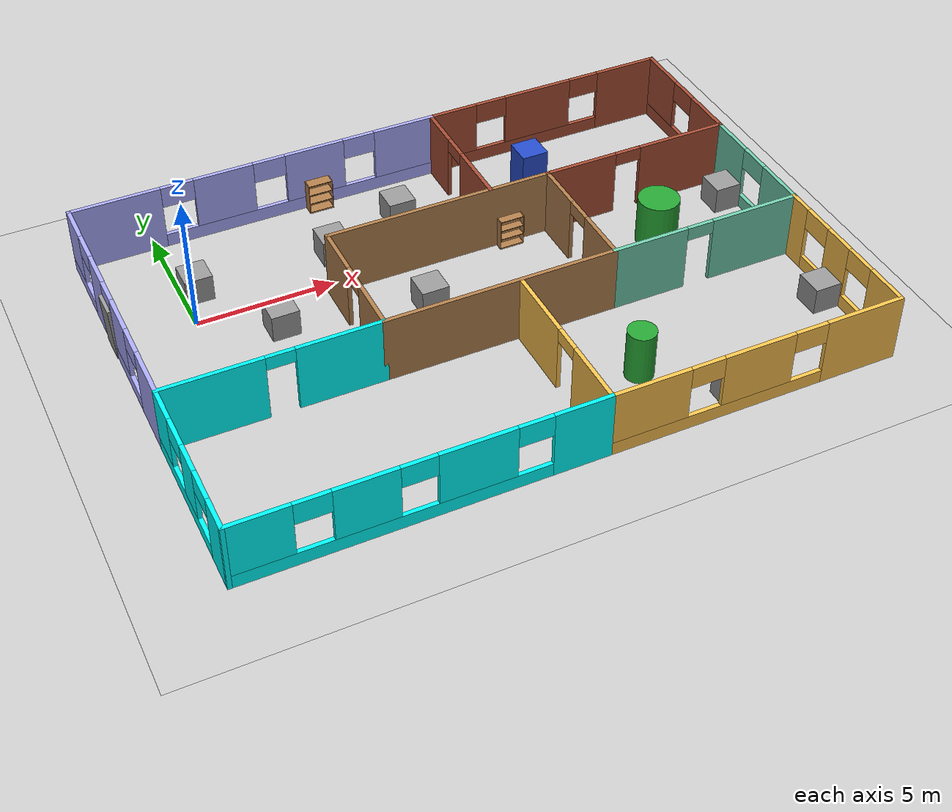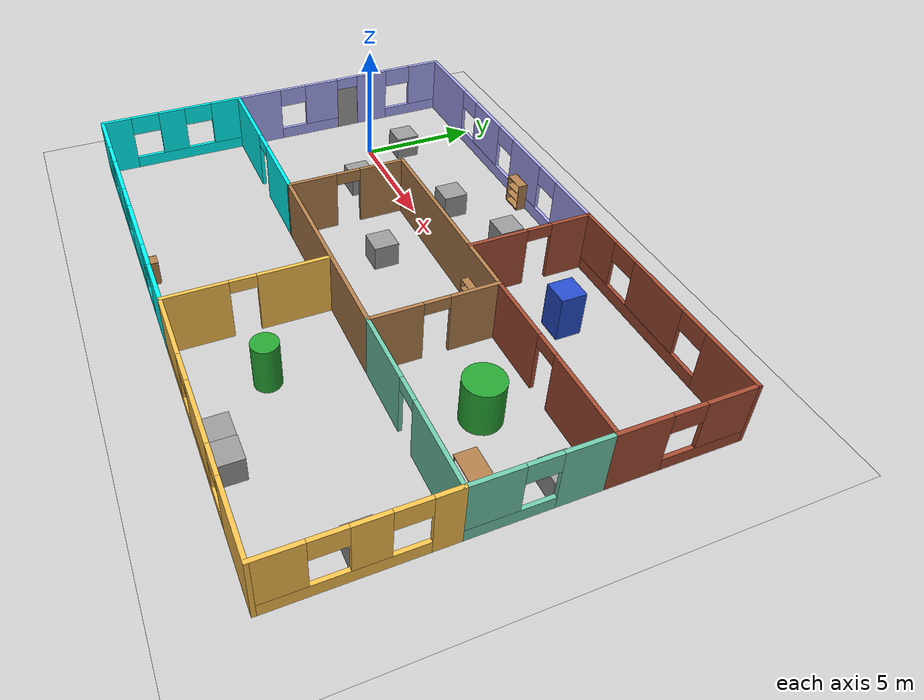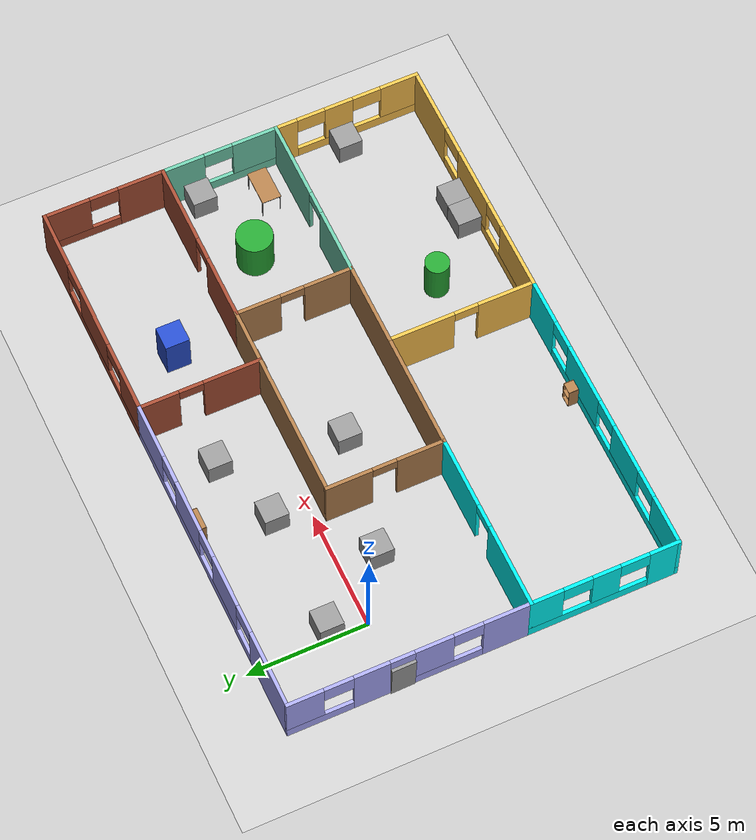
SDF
<sdf version="1.6">
 <world name="default">
  <plugin name="world" filename="libworld.so"/>
  <light name="sun" type="directional">
   <pose>0 0 10 0 -0 0</pose>
   <diffuse>0.8 0.8 0.8 1</diffuse>
   <specular>0.2 0.2 0.2 1</specular>
   <attenuation>
    <range>1000</range>
    <constant>0.9</constant>
    <linear>0.01</linear>
    <quadratic>0.001</quadratic>
   </attenuation>
   <direction>-0.5 0.1 -0.9</direction>
  </light>
  <model name="ground_plane">
   <static>1</static>
   <link name="link">
    <collision name="collision">
     <geometry><plane><normal>0 0 1</normal><size>100 100</size></plane></geometry>
     <surface><friction><ode><mu>100</mu><mu2>50</mu2></ode></friction></surface>
    </collision>
    <visual name="visual">
     <cast_shadows>0</cast_shadows>
     <geometry><plane><normal>0 0 1</normal><size>100 100</size></plane></geometry>
     <material>
      <script><uri>file://media/materials/scripts/gazebo.material</uri><name>Gazebo/Grey</name></script>
     </material>
    </visual>
   </link>
  </model>
  <gravity>0 0 -9.8</gravity>
  <magnetic_field>6e-06 2.3e-05 -4.2e-05</magnetic_field>
  <atmosphere type="adiabatic"/>
  <physics name="default_physics" default="0" type="ode">
   <max_step_size>0.001</max_step_size>
   <real_time_factor>1</real_time_factor>
   <real_time_update_rate>1000</real_time_update_rate>
  </physics>
  <scene><ambient>0.4 0.4 0.4 1</ambient><background>0.7 0.7 0.7 1</background><shadows>1</shadows></scene>
  <audio><device>default</device></audio>
  <spherical_coordinates>
   <surface_model>EARTH_WGS84</surface_model>
   <latitude_deg>0</latitude_deg>
   <longitude_deg>0</longitude_deg>
   <elevation>0</elevation>
   <heading_deg>0</heading_deg>
  </spherical_coordinates>
  <model name="prj1_building">
   <pose>8.66676 -3.41267 0 0 -0 0</pose>
   <link name="Wall_0">
    <collision name="Wall_0_Collision">
     <geometry><box><size>8.5 0.15 2.5</size></box></geometry>
     <pose>0 0 1.25 0 -0 0</pose>
    </collision>
    <visual name="Wall_0_Visual">
     <pose>0 0 1.25 0 -0 0</pose>
     <geometry><box><size>8.5 0.15 2.5</size></box></geometry>
     <material>
      <script><uri>file://media/materials/scripts/gazebo.material</uri><name>Gazebo/Wood</name></script>
      <ambient>1 1 1 1</ambient>
     </material>
     <meta><layer>0</layer></meta>
    </visual>
    <pose>0.2 -1.875 0 0 -0 0</pose>
   </link>
   <link name="Wall_13">
    <pose>11.475 5.46466 0 0 -0 1.5708</pose>
    <visual name="Wall_13_Visual_0">
     <pose>-1.56923 0 1.25 0 -0 0</pose>
     <geometry><box><size>1.99086 0.15 2.5</size></box></geometry>
     <material>
      <script><uri>file://media/materials/scripts/gazebo.material</uri><name>Gazebo/Bricks</name></script>
      <ambient>1 1 1 1</ambient>
     </material>
     <meta><layer>0</layer></meta>
    </visual>
    <collision name="Wall_13_Collision_0">
     <geometry><box><size>1.99086 0.15 2.5</size></box></geometry>
     <pose>-1.56923 0 1.25 0 -0 0</pose>
    </collision>
    <visual name="Wall_13_Visual_1">
     <pose>0.995431 0 0.25 0 -0 0</pose>
     <geometry><box><size>3.13846 0.15 0.5</size></box></geometry>
     <material>
      <script><uri>file://media/materials/scripts/gazebo.material</uri><name>Gazebo/Bricks</name></script>
      <ambient>1 1 1 1</ambient>
     </material>
     <meta><layer>0</layer></meta>
    </visual>
    <collision name="Wall_13_Collision_1">
     <geometry><box><size>3.13846 0.15 0.5</size></box></geometry>
     <pose>0.995431 0 0.25 0 -0 0</pose>
    </collision>
    <visual name="Wall_13_Visual_2">
     <pose>1.59543 0 1.5 0 -0 0</pose>
     <geometry><box><size>1.93846 0.15 2</size></box></geometry>
     <material>
      <script><uri>file://media/materials/scripts/gazebo.material</uri><name>Gazebo/Bricks</name></script>
      <ambient>1 1 1 1</ambient>
     </material>
     <meta><layer>0</layer></meta>
    </visual>
    <collision name="Wall_13_Collision_2">
     <geometry><box><size>1.93846 0.15 2</size></box></geometry>
     <pose>1.59543 0 1.5 0 -0 0</pose>
    </collision>
    <visual name="Wall_13_Visual_3">
     <pose>0.026202 0 2.1 0 -0 0</pose>
     <geometry><box><size>1.2 0.15 0.8</size></box></geometry>
     <material>
      <script><uri>file://media/materials/scripts/gazebo.material</uri><name>Gazebo/Bricks</name></script>
      <ambient>1 1 1 1</ambient>
     </material>
     <meta><layer>0</layer></meta>
    </visual>
    <collision name="Wall_13_Collision_3">
     <geometry><box><size>1.2 0.15 0.8</size></box></geometry>
     <pose>0.026202 0 2.1 0 -0 0</pose>
    </collision>
   </link>
   <link name="Wall_14">
    <pose>6.8 7.97443 0 0 -0 3.14159</pose>
    <visual name="Wall_14_Visual_0">
     <pose>-3.50992 0 1.25 0 -0 0</pose>
     <geometry><box><size>2.48016 0.15 2.5</size></box></geometry>
     <material>
      <script><uri>file://media/materials/scripts/gazebo.material</uri><name>Gazebo/Bricks</name></script>
      <ambient>1 1 1 1</ambient>
     </material>
     <meta><layer>0</layer></meta>
    </visual>
    <collision name="Wall_14_Collision_0">
     <geometry><box><size>2.48016 0.15 2.5</size></box></geometry>
     <pose>-3.50992 0 1.25 0 -0 0</pose>
    </collision>
    <visual name="Wall_14_Visual_1">
     <pose>1.24008 0 0.25 0 -0 0</pose>
     <geometry><box><size>7.01984 0.15 0.5</size></box></geometry>
     <material>
      <script><uri>file://media/materials/scripts/gazebo.material</uri><name>Gazebo/Bricks</name></script>
      <ambient>1 1 1 1</ambient>
     </material>
     <meta><layer>0</layer></meta>
    </visual>
    <collision name="Wall_14_Collision_1">
     <geometry><box><size>7.01984 0.15 0.5</size></box></geometry>
     <pose>1.24008 0 0.25 0 -0 0</pose>
    </collision>
    <visual name="Wall_14_Visual_2">
     <pose>0.282584 0 1.5 0 -0 0</pose>
     <geometry><box><size>2.70484 0.15 2</size></box></geometry>
     <material>
      <script><uri>file://media/materials/scripts/gazebo.material</uri><name>Gazebo/Bricks</name></script>
      <ambient>1 1 1 1</ambient>
     </material>
     <meta><layer>0</layer></meta>
    </visual>
    <collision name="Wall_14_Collision_2">
     <geometry><box><size>2.70484 0.15 2</size></box></geometry>
     <pose>0.282584 0 1.5 0 -0 0</pose>
    </collision>
    <visual name="Wall_14_Visual_3">
     <pose>3.7925 0 1.5 0 -0 0</pose>
     <geometry><box><size>1.915 0.15 2</size></box></geometry>
     <material>
      <script><uri>file://media/materials/scripts/gazebo.material</uri><name>Gazebo/Bricks</name></script>
      <ambient>1 1 1 1</ambient>
     </material>
     <meta><layer>0</layer></meta>
    </visual>
    <collision name="Wall_14_Collision_3">
     <geometry><box><size>1.915 0.15 2</size></box></geometry>
     <pose>3.7925 0 1.5 0 -0 0</pose>
    </collision>
    <visual name="Wall_14_Visual_4">
     <pose>-1.66984 0 2.1 0 -0 0</pose>
     <geometry><box><size>1.2 0.15 0.8</size></box></geometry>
     <material>
      <script><uri>file://media/materials/scripts/gazebo.material</uri><name>Gazebo/Bricks</name></script>
      <ambient>1 1 1 1</ambient>
     </material>
     <meta><layer>0</layer></meta>
    </visual>
    <collision name="Wall_14_Collision_4">
     <geometry><box><size>1.2 0.15 0.8</size></box></geometry>
     <pose>-1.66984 0 2.1 0 -0 0</pose>
    </collision>
    <visual name="Wall_14_Visual_5">
     <pose>2.23501 0 2.1 0 -0 0</pose>
     <geometry><box><size>1.2 0.15 0.8</size></box></geometry>
     <material>
      <script><uri>file://media/materials/scripts/gazebo.material</uri><name>Gazebo/Bricks</name></script>
      <ambient>1 1 1 1</ambient>
     </material>
     <meta><layer>0</layer></meta>
    </visual>
    <collision name="Wall_14_Collision_5">
     <geometry><box><size>1.2 0.15 0.8</size></box></geometry>
     <pose>2.23501 0 2.1 0 -0 0</pose>
    </collision>
   </link>
   <link name="Wall_15">
    <pose>2.125 5.46466 0 0 -0 -1.5708</pose>
    <visual name="Wall_15_Visual_0">
     <pose>-1.72519 0 1.25 0 -0 0</pose>
     <geometry><box><size>1.67895 0.15 2.5</size></box></geometry>
     <material>
      <script><uri>file://media/materials/scripts/gazebo.material</uri><name>Gazebo/Bricks</name></script>
      <ambient>1 1 1 1</ambient>
     </material>
     <meta><layer>0</layer></meta>
    </visual>
    <collision name="Wall_15_Collision_0">
     <geometry><box><size>1.67895 0.15 2.5</size></box></geometry>
     <pose>-1.72519 0 1.25 0 -0 0</pose>
    </collision>
    <visual name="Wall_15_Visual_1">
     <pose>1.33947 0 1.25 0 -0 0</pose>
     <geometry><box><size>2.45037 0.15 2.5</size></box></geometry>
     <material>
      <script><uri>file://media/materials/scripts/gazebo.material</uri><name>Gazebo/Bricks</name></script>
      <ambient>1 1 1 1</ambient>
     </material>
     <meta><layer>0</layer></meta>
    </visual>
    <collision name="Wall_15_Collision_1">
     <geometry><box><size>2.45037 0.15 2.5</size></box></geometry>
     <pose>1.33947 0 1.25 0 -0 0</pose>
    </collision>
    <visual name="Wall_15_Visual_2">
     <pose>-0.385714 0 2.25 0 -0 0</pose>
     <geometry><box><size>1 0.15 0.5</size></box></geometry>
     <material>
      <script><uri>file://media/materials/scripts/gazebo.material</uri><name>Gazebo/Bricks</name></script>
      <ambient>1 1 1 1</ambient>
     </material>
     <meta><layer>0</layer></meta>
    </visual>
    <collision name="Wall_15_Collision_2">
     <geometry><box><size>1 0.15 0.5</size></box></geometry>
     <pose>-0.385714 0 2.25 0 -0 0</pose>
    </collision>
   </link>
   <link name="Wall_2">
    <pose>-3.975 0.55 0 0 -0 1.5708</pose>
    <visual name="Wall_2_Visual_0">
     <pose>-1.47865 0 1.25 0 -0 0</pose>
     <geometry><box><size>2.0427 0.15 2.5</size></box></geometry>
     <material>
      <script><uri>file://media/materials/scripts/gazebo.material</uri><name>Gazebo/Wood</name></script>
      <ambient>1 1 1 1</ambient>
     </material>
     <meta><layer>0</layer></meta>
    </visual>
    <collision name="Wall_2_Collision_0">
     <geometry><box><size>2.0427 0.15 2.5</size></box></geometry>
     <pose>-1.47865 0 1.25 0 -0 0</pose>
    </collision>
    <visual name="Wall_2_Visual_1">
     <pose>1.52135 0 1.25 0 -0 0</pose>
     <geometry><box><size>1.9573 0.15 2.5</size></box></geometry>
     <material>
      <script><uri>file://media/materials/scripts/gazebo.material</uri><name>Gazebo/Wood</name></script>
      <ambient>1 1 1 1</ambient>
     </material>
     <meta><layer>0</layer></meta>
    </visual>
    <collision name="Wall_2_Collision_1">
     <geometry><box><size>1.9573 0.15 2.5</size></box></geometry>
     <pose>1.52135 0 1.25 0 -0 0</pose>
    </collision>
    <visual name="Wall_2_Visual_2">
     <pose>0.042704 0 2.25 0 -0 0</pose>
     <geometry><box><size>1 0.15 0.5</size></box></geometry>
     <material>
      <script><uri>file://media/materials/scripts/gazebo.material</uri><name>Gazebo/Wood</name></script>
      <ambient>1 1 1 1</ambient>
     </material>
     <meta><layer>0</layer></meta>
    </visual>
    <collision name="Wall_2_Collision_2">
     <geometry><box><size>1 0.15 0.5</size></box></geometry>
     <pose>0.042704 0 2.25 0 -0 0</pose>
    </collision>
   </link>
   <link name="Wall_25">
    <pose>11.475 0.55 0 0 -0 -1.5708</pose>
    <visual name="Wall_25_Visual_0">
     <pose>-1.58607 0 1.25 0 -0 0</pose>
     <geometry><box><size>1.82787 0.15 2.5</size></box></geometry>
     <material>
      <script><uri>file://media/materials/scripts/gazebo.material</uri><name>Gazebo/Grey</name></script>
      <ambient>0.435294 0.796078 0.67451 1</ambient>
     </material>
     <meta><layer>0</layer></meta>
    </visual>
    <collision name="Wall_25_Collision_0">
     <geometry><box><size>1.82787 0.15 2.5</size></box></geometry>
     <pose>-1.58607 0 1.25 0 -0 0</pose>
    </collision>
    <visual name="Wall_25_Visual_1">
     <pose>0.913933 0 0.25 0 -0 0</pose>
     <geometry><box><size>3.17213 0.15 0.5</size></box></geometry>
     <material>
      <script><uri>file://media/materials/scripts/gazebo.material</uri><name>Gazebo/Grey</name></script>
      <ambient>0.435294 0.796078 0.67451 1</ambient>
     </material>
     <meta><layer>0</layer></meta>
    </visual>
    <collision name="Wall_25_Collision_1">
     <geometry><box><size>3.17213 0.15 0.5</size></box></geometry>
     <pose>0.913933 0 0.25 0 -0 0</pose>
    </collision>
    <visual name="Wall_25_Visual_2">
     <pose>1.51393 0 1.5 0 -0 0</pose>
     <geometry><box><size>1.97213 0.15 2</size></box></geometry>
     <material>
      <script><uri>file://media/materials/scripts/gazebo.material</uri><name>Gazebo/Grey</name></script>
      <ambient>0.435294 0.796078 0.67451 1</ambient>
     </material>
     <meta><layer>0</layer></meta>
    </visual>
    <collision name="Wall_25_Collision_2">
     <geometry><box><size>1.97213 0.15 2</size></box></geometry>
     <pose>1.51393 0 1.5 0 -0 0</pose>
    </collision>
    <visual name="Wall_25_Visual_3">
     <pose>-0.072133 0 2.1 0 -0 0</pose>
     <geometry><box><size>1.2 0.15 0.8</size></box></geometry>
     <material>
      <script><uri>file://media/materials/scripts/gazebo.material</uri><name>Gazebo/Grey</name></script>
      <ambient>0.435294 0.796078 0.67451 1</ambient>
     </material>
     <meta><layer>0</layer></meta>
    </visual>
    <collision name="Wall_25_Collision_3">
     <geometry><box><size>1.2 0.15 0.8</size></box></geometry>
     <pose>-0.072133 0 2.1 0 -0 0</pose>
    </collision>
   </link>
   <link name="Wall_26">
    <pose>7.925 -1.875 0 0 -0 3.14159</pose>
    <visual name="Wall_26_Visual_0">
     <pose>-1.93285 0 1.25 0 -0 0</pose>
     <geometry><box><size>3.3843 0.15 2.5</size></box></geometry>
     <material>
      <script><uri>file://media/materials/scripts/gazebo.material</uri><name>Gazebo/Grey</name></script>
      <ambient>0.435294 0.796078 0.67451 1</ambient>
     </material>
     <meta><layer>0</layer></meta>
    </visual>
    <collision name="Wall_26_Collision_0">
     <geometry><box><size>3.3843 0.15 2.5</size></box></geometry>
     <pose>-1.93285 0 1.25 0 -0 0</pose>
    </collision>
    <visual name="Wall_26_Visual_1">
     <pose>2.19215 0 1.25 0 -0 0</pose>
     <geometry><box><size>2.8657 0.15 2.5</size></box></geometry>
     <material>
      <script><uri>file://media/materials/scripts/gazebo.material</uri><name>Gazebo/Grey</name></script>
      <ambient>0.435294 0.796078 0.67451 1</ambient>
     </material>
     <meta><layer>0</layer></meta>
    </visual>
    <collision name="Wall_26_Collision_1">
     <geometry><box><size>2.8657 0.15 2.5</size></box></geometry>
     <pose>2.19215 0 1.25 0 -0 0</pose>
    </collision>
    <visual name="Wall_26_Visual_2">
     <pose>0.259305 0 2.25 0 -0 0</pose>
     <geometry><box><size>1 0.15 0.5</size></box></geometry>
     <material>
      <script><uri>file://media/materials/scripts/gazebo.material</uri><name>Gazebo/Grey</name></script>
      <ambient>0.435294 0.796078 0.67451 1</ambient>
     </material>
     <meta><layer>0</layer></meta>
    </visual>
    <collision name="Wall_26_Collision_2">
     <geometry><box><size>1 0.15 0.5</size></box></geometry>
     <pose>0.259305 0 2.25 0 -0 0</pose>
    </collision>
   </link>
   <link name="Wall_28">
    <pose>11.475 -4.925 0 0 -0 -1.5708</pose>
    <visual name="Wall_28_Visual_0">
     <pose>-2.63878 0 1.25 0 -0 0</pose>
     <geometry><box><size>0.972448 0.15 2.5</size></box></geometry>
     <material>
      <script><uri>file://media/materials/scripts/gazebo.material</uri><name>Gazebo/Grey</name></script>
      <ambient>1 0.764706 0.305882 1</ambient>
     </material>
     <meta><layer>0</layer></meta>
    </visual>
    <collision name="Wall_28_Collision_0">
     <geometry><box><size>0.972448 0.15 2.5</size></box></geometry>
     <pose>-2.63878 0 1.25 0 -0 0</pose>
    </collision>
    <visual name="Wall_28_Visual_1">
     <pose>0.486224 0 0.25 0 -0 0</pose>
     <geometry><box><size>5.27755 0.15 0.5</size></box></geometry>
     <material>
      <script><uri>file://media/materials/scripts/gazebo.material</uri><name>Gazebo/Grey</name></script>
      <ambient>1 0.764706 0.305882 1</ambient>
     </material>
     <meta><layer>0</layer></meta>
    </visual>
    <collision name="Wall_28_Collision_1">
     <geometry><box><size>5.27755 0.15 0.5</size></box></geometry>
     <pose>0.486224 0 0.25 0 -0 0</pose>
    </collision>
    <visual name="Wall_28_Visual_2">
     <pose>-0.344238 0 1.5 0 -0 0</pose>
     <geometry><box><size>1.21663 0.15 2</size></box></geometry>
     <material>
      <script><uri>file://media/materials/scripts/gazebo.material</uri><name>Gazebo/Grey</name></script>
      <ambient>1 0.764706 0.305882 1</ambient>
     </material>
     <meta><layer>0</layer></meta>
    </visual>
    <collision name="Wall_28_Collision_2">
     <geometry><box><size>1.21663 0.15 2</size></box></geometry>
     <pose>-0.344238 0 1.5 0 -0 0</pose>
    </collision>
    <visual name="Wall_28_Visual_3">
     <pose>2.29454 0 1.5 0 -0 0</pose>
     <geometry><box><size>1.66092 0.15 2</size></box></geometry>
     <material>
      <script><uri>file://media/materials/scripts/gazebo.material</uri><name>Gazebo/Grey</name></script>
      <ambient>1 0.764706 0.305882 1</ambient>
     </material>
     <meta><layer>0</layer></meta>
    </visual>
    <collision name="Wall_28_Collision_3">
     <geometry><box><size>1.66092 0.15 2</size></box></geometry>
     <pose>2.29454 0 1.5 0 -0 0</pose>
    </collision>
    <visual name="Wall_28_Visual_4">
     <pose>-1.55255 0 2.1 0 -0 0</pose>
     <geometry><box><size>1.2 0.15 0.8</size></box></geometry>
     <material>
      <script><uri>file://media/materials/scripts/gazebo.material</uri><name>Gazebo/Grey</name></script>
      <ambient>1 0.764706 0.305882 1</ambient>
     </material>
     <meta><layer>0</layer></meta>
    </visual>
    <collision name="Wall_28_Collision_4">
     <geometry><box><size>1.2 0.15 0.8</size></box></geometry>
     <pose>-1.55255 0 2.1 0 -0 0</pose>
    </collision>
    <visual name="Wall_28_Visual_5">
     <pose>0.864076 0 2.1 0 -0 0</pose>
     <geometry><box><size>1.2 0.15 0.8</size></box></geometry>
     <material>
      <script><uri>file://media/materials/scripts/gazebo.material</uri><name>Gazebo/Grey</name></script>
      <ambient>1 0.764706 0.305882 1</ambient>
     </material>
     <meta><layer>0</layer></meta>
    </visual>
    <collision name="Wall_28_Collision_5">
     <geometry><box><size>1.2 0.15 0.8</size></box></geometry>
     <pose>0.864076 0 2.1 0 -0 0</pose>
    </collision>
   </link>
   <link name="Wall_34">
    <pose>6.175 -7.975 0 0 -0 3.14159</pose>
    <visual name="Wall_34_Visual_0">
     <pose>-3.92525 0 1.25 0 -0 0</pose>
     <geometry><box><size>2.89949 0.15 2.5</size></box></geometry>
     <material>
      <script><uri>file://media/materials/scripts/gazebo.material</uri><name>Gazebo/Grey</name></script>
      <ambient>1 0.764706 0.305882 1</ambient>
     </material>
     <meta><layer>0</layer></meta>
    </visual>
    <collision name="Wall_34_Collision_0">
     <geometry><box><size>2.89949 0.15 2.5</size></box></geometry>
     <pose>-3.92525 0 1.25 0 -0 0</pose>
    </collision>
    <visual name="Wall_34_Visual_1">
     <pose>1.44975 0 0.25 0 -0 0</pose>
     <geometry><box><size>7.85051 0.15 0.5</size></box></geometry>
     <material>
      <script><uri>file://media/materials/scripts/gazebo.material</uri><name>Gazebo/Grey</name></script>
      <ambient>1 0.764706 0.305882 1</ambient>
     </material>
     <meta><layer>0</layer></meta>
    </visual>
    <collision name="Wall_34_Collision_1">
     <geometry><box><size>7.85051 0.15 0.5</size></box></geometry>
     <pose>1.44975 0 0.25 0 -0 0</pose>
    </collision>
    <visual name="Wall_34_Visual_2">
     <pose>0.023833 0 1.5 0 -0 0</pose>
     <geometry><box><size>2.59868 0.15 2</size></box></geometry>
     <material>
      <script><uri>file://media/materials/scripts/gazebo.material</uri><name>Gazebo/Grey</name></script>
      <ambient>1 0.764706 0.305882 1</ambient>
     </material>
     <meta><layer>0</layer></meta>
    </visual>
    <collision name="Wall_34_Collision_2">
     <geometry><box><size>2.59868 0.15 2</size></box></geometry>
     <pose>0.023833 0 1.5 0 -0 0</pose>
    </collision>
    <visual name="Wall_34_Visual_3">
     <pose>3.94909 0 1.5 0 -0 0</pose>
     <geometry><box><size>2.85183 0.15 2</size></box></geometry>
     <material>
      <script><uri>file://media/materials/scripts/gazebo.material</uri><name>Gazebo/Grey</name></script>
      <ambient>1 0.764706 0.305882 1</ambient>
     </material>
     <meta><layer>0</layer></meta>
    </visual>
    <collision name="Wall_34_Collision_3">
     <geometry><box><size>2.85183 0.15 2</size></box></geometry>
     <pose>3.94909 0 1.5 0 -0 0</pose>
    </collision>
    <visual name="Wall_34_Visual_4">
     <pose>-1.8755 0 2.1 0 -0 0</pose>
     <geometry><box><size>1.2 0.15 0.8</size></box></geometry>
     <material>
      <script><uri>file://media/materials/scripts/gazebo.material</uri><name>Gazebo/Grey</name></script>
      <ambient>1 0.764706 0.305882 1</ambient>
     </material>
     <meta><layer>0</layer></meta>
    </visual>
    <collision name="Wall_34_Collision_4">
     <geometry><box><size>1.2 0.15 0.8</size></box></geometry>
     <pose>-1.8755 0 2.1 0 -0 0</pose>
    </collision>
    <visual name="Wall_34_Visual_5">
     <pose>1.92317 0 2.1 0 -0 0</pose>
     <geometry><box><size>1.2 0.15 0.8</size></box></geometry>
     <material>
      <script><uri>file://media/materials/scripts/gazebo.material</uri><name>Gazebo/Grey</name></script>
      <ambient>1 0.764706 0.305882 1</ambient>
     </material>
     <meta><layer>0</layer></meta>
    </visual>
    <collision name="Wall_34_Collision_5">
     <geometry><box><size>1.2 0.15 0.8</size></box></geometry>
     <pose>1.92317 0 2.1 0 -0 0</pose>
    </collision>
   </link>
   <link name="Wall_35">
    <pose>0.875 -4.925 0 0 -0 1.5708</pose>
    <visual name="Wall_35_Visual_0">
     <pose>-1.90603 0 1.25 0 -0 0</pose>
     <geometry><box><size>2.43795 0.15 2.5</size></box></geometry>
     <material>
      <script><uri>file://media/materials/scripts/gazebo.material</uri><name>Gazebo/Grey</name></script>
      <ambient>1 0.764706 0.305882 1</ambient>
     </material>
     <meta><layer>0</layer></meta>
    </visual>
    <collision name="Wall_35_Collision_0">
     <geometry><box><size>2.43795 0.15 2.5</size></box></geometry>
     <pose>-1.90603 0 1.25 0 -0 0</pose>
    </collision>
    <visual name="Wall_35_Visual_1">
     <pose>1.71897 0 1.25 0 -0 0</pose>
     <geometry><box><size>2.81205 0.15 2.5</size></box></geometry>
     <material>
      <script><uri>file://media/materials/scripts/gazebo.material</uri><name>Gazebo/Grey</name></script>
      <ambient>1 0.764706 0.305882 1</ambient>
     </material>
     <meta><layer>0</layer></meta>
    </visual>
    <collision name="Wall_35_Collision_1">
     <geometry><box><size>2.81205 0.15 2.5</size></box></geometry>
     <pose>1.71897 0 1.25 0 -0 0</pose>
    </collision>
    <visual name="Wall_35_Visual_2">
     <pose>-0.187052 0 2.25 0 -0 0</pose>
     <geometry><box><size>1 0.15 0.5</size></box></geometry>
     <material>
      <script><uri>file://media/materials/scripts/gazebo.material</uri><name>Gazebo/Grey</name></script>
      <ambient>1 0.764706 0.305882 1</ambient>
     </material>
     <meta><layer>0</layer></meta>
    </visual>
    <collision name="Wall_35_Collision_2">
     <geometry><box><size>1 0.15 0.5</size></box></geometry>
     <pose>-0.187052 0 2.25 0 -0 0</pose>
    </collision>
   </link>
   <link name="Wall_37">
    <pose>-5.3 -7.975 0 0 -0 3.14159</pose>
    <visual name="Wall_37_Visual_0">
     <pose>-5.23153 0 1.25 0 -0 0</pose>
     <geometry><box><size>2.03695 0.15 2.5</size></box></geometry>
     <material>
      <script><uri>file://media/materials/scripts/gazebo.material</uri><name>Gazebo/Grey</name></script>
      <ambient>0 1 1 1</ambient>
     </material>
     <meta><layer>0</layer></meta>
    </visual>
    <collision name="Wall_37_Collision_0">
     <geometry><box><size>2.03695 0.15 2.5</size></box></geometry>
     <pose>-5.23153 0 1.25 0 -0 0</pose>
    </collision>
    <visual name="Wall_37_Visual_1">
     <pose>1.01848 0 0.25 0 -0 0</pose>
     <geometry><box><size>10.4631 0.15 0.5</size></box></geometry>
     <material>
      <script><uri>file://media/materials/scripts/gazebo.material</uri><name>Gazebo/Grey</name></script>
      <ambient>0 1 1 1</ambient>
     </material>
     <meta><layer>0</layer></meta>
    </visual>
    <collision name="Wall_37_Collision_1">
     <geometry><box><size>10.4631 0.15 0.5</size></box></geometry>
     <pose>1.01848 0 0.25 0 -0 0</pose>
    </collision>
    <visual name="Wall_37_Visual_2">
     <pose>-1.71371 0 1.5 0 -0 0</pose>
     <geometry><box><size>2.59868 0.15 2</size></box></geometry>
     <material>
      <script><uri>file://media/materials/scripts/gazebo.material</uri><name>Gazebo/Grey</name></script>
      <ambient>0 1 1 1</ambient>
     </material>
     <meta><layer>0</layer></meta>
    </visual>
    <collision name="Wall_37_Collision_2">
     <geometry><box><size>2.59868 0.15 2</size></box></geometry>
     <pose>-1.71371 0 1.5 0 -0 0</pose>
    </collision>
    <visual name="Wall_37_Visual_3">
     <pose>1.84421 0 1.5 0 -0 0</pose>
     <geometry><box><size>2.11715 0.15 2</size></box></geometry>
     <material>
      <script><uri>file://media/materials/scripts/gazebo.material</uri><name>Gazebo/Grey</name></script>
      <ambient>0 1 1 1</ambient>
     </material>
     <meta><layer>0</layer></meta>
    </visual>
    <collision name="Wall_37_Collision_3">
     <geometry><box><size>2.11715 0.15 2</size></box></geometry>
     <pose>1.84421 0 1.5 0 -0 0</pose>
    </collision>
    <visual name="Wall_37_Visual_4">
     <pose>5.17639 0 1.5 0 -0 0</pose>
     <geometry><box><size>2.14722 0.15 2</size></box></geometry>
     <material>
      <script><uri>file://media/materials/scripts/gazebo.material</uri><name>Gazebo/Grey</name></script>
      <ambient>0 1 1 1</ambient>
     </material>
     <meta><layer>0</layer></meta>
    </visual>
    <collision name="Wall_37_Collision_4">
     <geometry><box><size>2.14722 0.15 2</size></box></geometry>
     <pose>5.17639 0 1.5 0 -0 0</pose>
    </collision>
    <visual name="Wall_37_Visual_5">
     <pose>-3.61305 0 2.1 0 -0 0</pose>
     <geometry><box><size>1.2 0.15 0.8</size></box></geometry>
     <material>
      <script><uri>file://media/materials/scripts/gazebo.material</uri><name>Gazebo/Grey</name></script>
      <ambient>0 1 1 1</ambient>
     </material>
     <meta><layer>0</layer></meta>
    </visual>
    <collision name="Wall_37_Collision_5">
     <geometry><box><size>1.2 0.15 0.8</size></box></geometry>
     <pose>-3.61305 0 2.1 0 -0 0</pose>
    </collision>
    <visual name="Wall_37_Visual_6">
     <pose>0.185627 0 2.1 0 -0 0</pose>
     <geometry><box><size>1.2 0.15 0.8</size></box></geometry>
     <material>
      <script><uri>file://media/materials/scripts/gazebo.material</uri><name>Gazebo/Grey</name></script>
      <ambient>0 1 1 1</ambient>
     </material>
     <meta><layer>0</layer></meta>
    </visual>
    <collision name="Wall_37_Collision_6">
     <geometry><box><size>1.2 0.15 0.8</size></box></geometry>
     <pose>0.185627 0 2.1 0 -0 0</pose>
    </collision>
    <visual name="Wall_37_Visual_7">
     <pose>3.50278 0 2.1 0 -0 0</pose>
     <geometry><box><size>1.2 0.15 0.8</size></box></geometry>
     <material>
      <script><uri>file://media/materials/scripts/gazebo.material</uri><name>Gazebo/Grey</name></script>
      <ambient>0 1 1 1</ambient>
     </material>
     <meta><layer>0</layer></meta>
    </visual>
    <collision name="Wall_37_Collision_7">
     <geometry><box><size>1.2 0.15 0.8</size></box></geometry>
     <pose>3.50278 0 2.1 0 -0 0</pose>
    </collision>
   </link>
   <link name="Wall_38">
    <pose>-11.475 -4.925 0 0 -0 1.5708</pose>
    <visual name="Wall_38_Visual_0">
     <pose>-2.47808 0 1.25 0 -0 0</pose>
     <geometry><box><size>1.29384 0.15 2.5</size></box></geometry>
     <material>
      <script><uri>file://media/materials/scripts/gazebo.material</uri><name>Gazebo/Grey</name></script>
      <ambient>0 1 1 1</ambient>
     </material>
     <meta><layer>0</layer></meta>
    </visual>
    <collision name="Wall_38_Collision_0">
     <geometry><box><size>1.29384 0.15 2.5</size></box></geometry>
     <pose>-2.47808 0 1.25 0 -0 0</pose>
    </collision>
    <visual name="Wall_38_Visual_1">
     <pose>0.646921 0 0.25 0 -0 0</pose>
     <geometry><box><size>4.95616 0.15 0.5</size></box></geometry>
     <material>
      <script><uri>file://media/materials/scripts/gazebo.material</uri><name>Gazebo/Grey</name></script>
      <ambient>0 1 1 1</ambient>
     </material>
     <meta><layer>0</layer></meta>
    </visual>
    <collision name="Wall_38_Collision_1">
     <geometry><box><size>4.95616 0.15 0.5</size></box></geometry>
     <pose>0.646921 0 0.25 0 -0 0</pose>
    </collision>
    <visual name="Wall_38_Visual_2">
     <pose>-0.053435 0 1.5 0 -0 0</pose>
     <geometry><box><size>1.15545 0.15 2</size></box></geometry>
     <material>
      <script><uri>file://media/materials/scripts/gazebo.material</uri><name>Gazebo/Grey</name></script>
      <ambient>0 1 1 1</ambient>
     </material>
     <meta><layer>0</layer></meta>
    </visual>
    <collision name="Wall_38_Collision_2">
     <geometry><box><size>1.15545 0.15 2</size></box></geometry>
     <pose>-0.053435 0 1.5 0 -0 0</pose>
    </collision>
    <visual name="Wall_38_Visual_3">
     <pose>2.42464 0 1.5 0 -0 0</pose>
     <geometry><box><size>1.40071 0.15 2</size></box></geometry>
     <material>
      <script><uri>file://media/materials/scripts/gazebo.material</uri><name>Gazebo/Grey</name></script>
      <ambient>0 1 1 1</ambient>
     </material>
     <meta><layer>0</layer></meta>
    </visual>
    <collision name="Wall_38_Collision_3">
     <geometry><box><size>1.40071 0.15 2</size></box></geometry>
     <pose>2.42464 0 1.5 0 -0 0</pose>
    </collision>
    <visual name="Wall_38_Visual_4">
     <pose>-1.23116 0 2.1 0 -0 0</pose>
     <geometry><box><size>1.2 0.15 0.8</size></box></geometry>
     <material>
      <script><uri>file://media/materials/scripts/gazebo.material</uri><name>Gazebo/Grey</name></script>
      <ambient>0 1 1 1</ambient>
     </material>
     <meta><layer>0</layer></meta>
    </visual>
    <collision name="Wall_38_Collision_4">
     <geometry><box><size>1.2 0.15 0.8</size></box></geometry>
     <pose>-1.23116 0 2.1 0 -0 0</pose>
    </collision>
    <visual name="Wall_38_Visual_5">
     <pose>1.12429 0 2.1 0 -0 0</pose>
     <geometry><box><size>1.2 0.15 0.8</size></box></geometry>
     <material>
      <script><uri>file://media/materials/scripts/gazebo.material</uri><name>Gazebo/Grey</name></script>
      <ambient>0 1 1 1</ambient>
     </material>
     <meta><layer>0</layer></meta>
    </visual>
    <collision name="Wall_38_Collision_5">
     <geometry><box><size>1.2 0.15 0.8</size></box></geometry>
     <pose>1.12429 0 2.1 0 -0 0</pose>
    </collision>
   </link>
   <link name="Wall_39">
    <pose>-7.725 -1.875 0 0 -0 0</pose>
    <visual name="Wall_39_Visual_0">
     <pose>-2.03776 0 1.25 0 -0 0</pose>
     <geometry><box><size>3.57449 0.15 2.5</size></box></geometry>
     <material>
      <script><uri>file://media/materials/scripts/gazebo.material</uri><name>Gazebo/Grey</name></script>
      <ambient>0 1 1 1</ambient>
     </material>
     <meta><layer>0</layer></meta>
    </visual>
    <collision name="Wall_39_Collision_0">
     <geometry><box><size>3.57449 0.15 2.5</size></box></geometry>
     <pose>-2.03776 0 1.25 0 -0 0</pose>
    </collision>
    <visual name="Wall_39_Visual_1">
     <pose>2.28724 0 1.25 0 -0 0</pose>
     <geometry><box><size>3.07551 0.15 2.5</size></box></geometry>
     <material>
      <script><uri>file://media/materials/scripts/gazebo.material</uri><name>Gazebo/Grey</name></script>
      <ambient>0 1 1 1</ambient>
     </material>
     <meta><layer>0</layer></meta>
    </visual>
    <collision name="Wall_39_Collision_1">
     <geometry><box><size>3.07551 0.15 2.5</size></box></geometry>
     <pose>2.28724 0 1.25 0 -0 0</pose>
    </collision>
    <visual name="Wall_39_Visual_2">
     <pose>0.249486 0 2.25 0 -0 0</pose>
     <geometry><box><size>1 0.15 0.5</size></box></geometry>
     <material>
      <script><uri>file://media/materials/scripts/gazebo.material</uri><name>Gazebo/Grey</name></script>
      <ambient>0 1 1 1</ambient>
     </material>
     <meta><layer>0</layer></meta>
    </visual>
    <collision name="Wall_39_Collision_2">
     <geometry><box><size>1 0.15 0.5</size></box></geometry>
     <pose>0.249486 0 2.25 0 -0 0</pose>
    </collision>
   </link>
   <link name="Wall_41">
    <pose>-11.475 3.05 0 0 -0 1.5708</pose>
    <visual name="Wall_41_Visual_0">
     <pose>-3.98718 0 1.25 0 -0 0</pose>
     <geometry><box><size>2.02564 0.15 2.5</size></box></geometry>
     <material>
      <script><uri>file://media/materials/scripts/gazebo.material</uri><name>Gazebo/Grey</name></script>
      <ambient>0.666667 0.666667 1 1</ambient>
     </material>
     <meta><layer>0</layer></meta>
    </visual>
    <collision name="Wall_41_Collision_0">
     <geometry><box><size>2.02564 0.15 2.5</size></box></geometry>
     <pose>-3.98718 0 1.25 0 -0 0</pose>
    </collision>
    <visual name="Wall_41_Visual_1">
     <pose>1.53482 0 1.25 0 -0 0</pose>
     <geometry><box><size>1.46812 0.15 2.5</size></box></geometry>
     <material>
      <script><uri>file://media/materials/scripts/gazebo.material</uri><name>Gazebo/Grey</name></script>
      <ambient>0.666667 0.666667 1 1</ambient>
     </material>
     <meta><layer>0</layer></meta>
    </visual>
    <collision name="Wall_41_Collision_1">
     <geometry><box><size>1.46812 0.15 2.5</size></box></geometry>
     <pose>1.53482 0 1.25 0 -0 0</pose>
    </collision>
    <visual name="Wall_41_Visual_2">
     <pose>-1.5868 0 0.25 0 -0 0</pose>
     <geometry><box><size>2.77513 0.15 0.5</size></box></geometry>
     <material>
      <script><uri>file://media/materials/scripts/gazebo.material</uri><name>Gazebo/Grey</name></script>
      <ambient>0.666667 0.666667 1 1</ambient>
     </material>
     <meta><layer>0</layer></meta>
    </visual>
    <collision name="Wall_41_Collision_2">
     <geometry><box><size>2.77513 0.15 0.5</size></box></geometry>
     <pose>-1.5868 0 0.25 0 -0 0</pose>
    </collision>
    <visual name="Wall_41_Visual_3">
     <pose>3.63444 0 0.25 0 -0 0</pose>
     <geometry><box><size>2.73112 0.15 0.5</size></box></geometry>
     <material>
      <script><uri>file://media/materials/scripts/gazebo.material</uri><name>Gazebo/Grey</name></script>
      <ambient>0.666667 0.666667 1 1</ambient>
     </material>
     <meta><layer>0</layer></meta>
    </visual>
    <collision name="Wall_41_Collision_3">
     <geometry><box><size>2.73112 0.15 0.5</size></box></geometry>
     <pose>3.63444 0 0.25 0 -0 0</pose>
    </collision>
    <visual name="Wall_41_Visual_4">
     <pose>-0.986802 0 1.5 0 -0 0</pose>
     <geometry><box><size>1.57513 0.15 2</size></box></geometry>
     <material>
      <script><uri>file://media/materials/scripts/gazebo.material</uri><name>Gazebo/Grey</name></script>
      <ambient>0.666667 0.666667 1 1</ambient>
     </material>
     <meta><layer>0</layer></meta>
    </visual>
    <collision name="Wall_41_Collision_4">
     <geometry><box><size>1.57513 0.15 2</size></box></geometry>
     <pose>-0.986802 0 1.5 0 -0 0</pose>
    </collision>
    <visual name="Wall_41_Visual_5">
     <pose>-0.986802 0 1.5 0 -0 0</pose>
     <geometry><box><size>1.57513 0.15 2</size></box></geometry>
     <material>
      <script><uri>file://media/materials/scripts/gazebo.material</uri><name>Gazebo/Grey</name></script>
      <ambient>0.666667 0.666667 1 1</ambient>
     </material>
     <meta><layer>0</layer></meta>
    </visual>
    <collision name="Wall_41_Collision_5">
     <geometry><box><size>1.57513 0.15 2</size></box></geometry>
     <pose>-0.986802 0 1.5 0 -0 0</pose>
    </collision>
    <visual name="Wall_41_Visual_6">
     <pose>4.23444 0 1.5 0 -0 0</pose>
     <geometry><box><size>1.53112 0.15 2</size></box></geometry>
     <material>
      <script><uri>file://media/materials/scripts/gazebo.material</uri><name>Gazebo/Grey</name></script>
      <ambient>0.666667 0.666667 1 1</ambient>
     </material>
     <meta><layer>0</layer></meta>
    </visual>
    <collision name="Wall_41_Collision_6">
     <geometry><box><size>1.53112 0.15 2</size></box></geometry>
     <pose>4.23444 0 1.5 0 -0 0</pose>
    </collision>
    <visual name="Wall_41_Visual_7">
     <pose>-2.37436 0 2.1 0 -0 0</pose>
     <geometry><box><size>1.2 0.15 0.8</size></box></geometry>
     <material>
      <script><uri>file://media/materials/scripts/gazebo.material</uri><name>Gazebo/Grey</name></script>
      <ambient>0.666667 0.666667 1 1</ambient>
     </material>
     <meta><layer>0</layer></meta>
    </visual>
    <collision name="Wall_41_Collision_7">
     <geometry><box><size>1.2 0.15 0.8</size></box></geometry>
     <pose>-2.37436 0 2.1 0 -0 0</pose>
    </collision>
    <visual name="Wall_41_Visual_8">
     <pose>2.86888 0 2.1 0 -0 0</pose>
     <geometry><box><size>1.2 0.15 0.8</size></box></geometry>
     <material>
      <script><uri>file://media/materials/scripts/gazebo.material</uri><name>Gazebo/Grey</name></script>
      <ambient>0.666667 0.666667 1 1</ambient>
     </material>
     <meta><layer>0</layer></meta>
    </visual>
    <collision name="Wall_41_Collision_8">
     <geometry><box><size>1.2 0.15 0.8</size></box></geometry>
     <pose>2.86888 0 2.1 0 -0 0</pose>
    </collision>
    <visual name="Wall_41_Visual_9">
     <pose>0.300761 0 2.25 0 -0 0</pose>
     <geometry><box><size>1 0.15 0.5</size></box></geometry>
     <material>
      <script><uri>file://media/materials/scripts/gazebo.material</uri><name>Gazebo/Grey</name></script>
      <ambient>0.666667 0.666667 1 1</ambient>
     </material>
     <meta><layer>0</layer></meta>
    </visual>
    <collision name="Wall_41_Collision_9">
     <geometry><box><size>1 0.15 0.5</size></box></geometry>
     <pose>0.300761 0 2.25 0 -0 0</pose>
    </collision>
    <visual name="Wall_41_Visual_10">
     <pose>0.300761 0 2.25 0 -0 0</pose>
     <geometry><box><size>1 0.15 0.5</size></box></geometry>
     <material>
      <script><uri>file://media/materials/scripts/gazebo.material</uri><name>Gazebo/Grey</name></script>
      <ambient>0.666667 0.666667 1 1</ambient>
     </material>
     <meta><layer>0</layer></meta>
    </visual>
    <collision name="Wall_41_Collision_10">
     <geometry><box><size>1 0.15 0.5</size></box></geometry>
     <pose>0.300761 0 2.25 0 -0 0</pose>
    </collision>
   </link>
   <link name="Wall_42">
    <pose>-4.675 7.975 0 0 -0 0</pose>
    <visual name="Wall_42_Visual_0">
     <pose>-5.22102 0 1.25 0 -0 0</pose>
     <geometry><box><size>3.30796 0.15 2.5</size></box></geometry>
     <material>
      <script><uri>file://media/materials/scripts/gazebo.material</uri><name>Gazebo/Grey</name></script>
      <ambient>0.666667 0.666667 1 1</ambient>
     </material>
     <meta><layer>0</layer></meta>
    </visual>
    <collision name="Wall_42_Collision_0">
     <geometry><box><size>3.30796 0.15 2.5</size></box></geometry>
     <pose>-5.22102 0 1.25 0 -0 0</pose>
    </collision>
    <visual name="Wall_42_Visual_1">
     <pose>1.65398 0 0.25 0 -0 0</pose>
     <geometry><box><size>10.442 0.15 0.5</size></box></geometry>
     <material>
      <script><uri>file://media/materials/scripts/gazebo.material</uri><name>Gazebo/Grey</name></script>
      <ambient>0.666667 0.666667 1 1</ambient>
     </material>
     <meta><layer>0</layer></meta>
    </visual>
    <collision name="Wall_42_Collision_1">
     <geometry><box><size>10.442 0.15 0.5</size></box></geometry>
     <pose>1.65398 0 0.25 0 -0 0</pose>
    </collision>
    <visual name="Wall_42_Visual_2">
     <pose>-1.26087 0 1.5 0 -0 0</pose>
     <geometry><box><size>2.21234 0.15 2</size></box></geometry>
     <material>
      <script><uri>file://media/materials/scripts/gazebo.material</uri><name>Gazebo/Grey</name></script>
      <ambient>0.666667 0.666667 1 1</ambient>
     </material>
     <meta><layer>0</layer></meta>
    </visual>
    <collision name="Wall_42_Collision_2">
     <geometry><box><size>2.21234 0.15 2</size></box></geometry>
     <pose>-1.26087 0 1.5 0 -0 0</pose>
    </collision>
    <visual name="Wall_42_Visual_3">
     <pose>2.16906 0 1.5 0 -0 0</pose>
     <geometry><box><size>2.24752 0.15 2</size></box></geometry>
     <material>
      <script><uri>file://media/materials/scripts/gazebo.material</uri><name>Gazebo/Grey</name></script>
      <ambient>0.666667 0.666667 1 1</ambient>
     </material>
     <meta><layer>0</layer></meta>
    </visual>
    <collision name="Wall_42_Collision_3">
     <geometry><box><size>2.24752 0.15 2</size></box></geometry>
     <pose>2.16906 0 1.5 0 -0 0</pose>
    </collision>
    <visual name="Wall_42_Visual_4">
     <pose>5.68391 0 1.5 0 -0 0</pose>
     <geometry><box><size>2.38218 0.15 2</size></box></geometry>
     <material>
      <script><uri>file://media/materials/scripts/gazebo.material</uri><name>Gazebo/Grey</name></script>
      <ambient>0.666667 0.666667 1 1</ambient>
     </material>
     <meta><layer>0</layer></meta>
    </visual>
    <collision name="Wall_42_Collision_4">
     <geometry><box><size>2.38218 0.15 2</size></box></geometry>
     <pose>5.68391 0 1.5 0 -0 0</pose>
    </collision>
    <visual name="Wall_42_Visual_5">
     <pose>-2.96704 0 2.1 0 -0 0</pose>
     <geometry><box><size>1.2 0.15 0.8</size></box></geometry>
     <material>
      <script><uri>file://media/materials/scripts/gazebo.material</uri><name>Gazebo/Grey</name></script>
      <ambient>0.666667 0.666667 1 1</ambient>
     </material>
     <meta><layer>0</layer></meta>
    </visual>
    <collision name="Wall_42_Collision_5">
     <geometry><box><size>1.2 0.15 0.8</size></box></geometry>
     <pose>-2.96704 0 2.1 0 -0 0</pose>
    </collision>
    <visual name="Wall_42_Visual_6">
     <pose>0.445304 0 2.1 0 -0 0</pose>
     <geometry><box><size>1.2 0.15 0.8</size></box></geometry>
     <material>
      <script><uri>file://media/materials/scripts/gazebo.material</uri><name>Gazebo/Grey</name></script>
      <ambient>0.666667 0.666667 1 1</ambient>
     </material>
     <meta><layer>0</layer></meta>
    </visual>
    <collision name="Wall_42_Collision_6">
     <geometry><box><size>1.2 0.15 0.8</size></box></geometry>
     <pose>0.445304 0 2.1 0 -0 0</pose>
    </collision>
    <visual name="Wall_42_Visual_7">
     <pose>3.89282 0 2.1 0 -0 0</pose>
     <geometry><box><size>1.2 0.15 0.8</size></box></geometry>
     <material>
      <script><uri>file://media/materials/scripts/gazebo.material</uri><name>Gazebo/Grey</name></script>
      <ambient>0.666667 0.666667 1 1</ambient>
     </material>
     <meta><layer>0</layer></meta>
    </visual>
    <collision name="Wall_42_Collision_7">
     <geometry><box><size>1.2 0.15 0.8</size></box></geometry>
     <pose>3.89282 0 2.1 0 -0 0</pose>
    </collision>
   </link>
   <link name="Wall_5">
    <collision name="Wall_5_Collision">
     <geometry><box><size>8.5 0.15 2.5</size></box></geometry>
     <pose>0 0 1.25 0 -0 0</pose>
    </collision>
    <visual name="Wall_5_Visual">
     <pose>0 0 1.25 0 -0 0</pose>
     <geometry><box><size>8.5 0.15 2.5</size></box></geometry>
     <material>
      <script><uri>file://media/materials/scripts/gazebo.material</uri><name>Gazebo/Wood</name></script>
      <ambient>1 1 1 1</ambient>
     </material>
     <meta><layer>0</layer></meta>
    </visual>
    <pose>0.2 2.975 0 0 -0 0</pose>
   </link>
   <link name="Wall_6">
    <pose>4.375 0.55 0 0 -0 -1.5708</pose>
    <visual name="Wall_6_Visual_0">
     <pose>-1.54147 0 1.25 0 -0 0</pose>
     <geometry><box><size>1.91707 0.15 2.5</size></box></geometry>
     <material>
      <script><uri>file://media/materials/scripts/gazebo.material</uri><name>Gazebo/Wood</name></script>
      <ambient>1 1 1 1</ambient>
     </material>
     <meta><layer>0</layer></meta>
    </visual>
    <collision name="Wall_6_Collision_0">
     <geometry><box><size>1.91707 0.15 2.5</size></box></geometry>
     <pose>-1.54147 0 1.25 0 -0 0</pose>
    </collision>
    <visual name="Wall_6_Visual_1">
     <pose>1.45853 0 1.25 0 -0 0</pose>
     <geometry><box><size>2.08293 0.15 2.5</size></box></geometry>
     <material>
      <script><uri>file://media/materials/scripts/gazebo.material</uri><name>Gazebo/Wood</name></script>
      <ambient>1 1 1 1</ambient>
     </material>
     <meta><layer>0</layer></meta>
    </visual>
    <collision name="Wall_6_Collision_1">
     <geometry><box><size>2.08293 0.15 2.5</size></box></geometry>
     <pose>1.45853 0 1.25 0 -0 0</pose>
    </collision>
    <visual name="Wall_6_Visual_2">
     <pose>-0.082931 0 2.25 0 -0 0</pose>
     <geometry><box><size>1 0.15 0.5</size></box></geometry>
     <material>
      <script><uri>file://media/materials/scripts/gazebo.material</uri><name>Gazebo/Wood</name></script>
      <ambient>1 1 1 1</ambient>
     </material>
     <meta><layer>0</layer></meta>
    </visual>
    <collision name="Wall_6_Collision_2">
     <geometry><box><size>1 0.15 0.5</size></box></geometry>
     <pose>-0.082931 0 2.25 0 -0 0</pose>
    </collision>
   </link>
   <link name="Wall_9">
    <pose>7.925 2.975 0 0 -0 3.14159</pose>
    <visual name="Wall_9_Visual_0">
     <pose>-1.89755 0 1.25 0 -0 0</pose>
     <geometry><box><size>3.45491 0.15 2.5</size></box></geometry>
     <material>
      <script><uri>file://media/materials/scripts/gazebo.material</uri><name>Gazebo/Bricks</name></script>
      <ambient>1 1 1 1</ambient>
     </material>
     <meta><layer>0</layer></meta>
    </visual>
    <collision name="Wall_9_Collision_0">
     <geometry><box><size>3.45491 0.15 2.5</size></box></geometry>
     <pose>-1.89755 0 1.25 0 -0 0</pose>
    </collision>
    <visual name="Wall_9_Visual_1">
     <pose>2.22745 0 1.25 0 -0 0</pose>
     <geometry><box><size>2.79509 0.15 2.5</size></box></geometry>
     <material>
      <script><uri>file://media/materials/scripts/gazebo.material</uri><name>Gazebo/Bricks</name></script>
      <ambient>1 1 1 1</ambient>
     </material>
     <meta><layer>0</layer></meta>
    </visual>
    <collision name="Wall_9_Collision_1">
     <geometry><box><size>2.79509 0.15 2.5</size></box></geometry>
     <pose>2.22745 0 1.25 0 -0 0</pose>
    </collision>
    <visual name="Wall_9_Visual_2">
     <pose>0.32991 0 2.25 0 -0 0</pose>
     <geometry><box><size>1 0.15 0.5</size></box></geometry>
     <material>
      <script><uri>file://media/materials/scripts/gazebo.material</uri><name>Gazebo/Bricks</name></script>
      <ambient>1 1 1 1</ambient>
     </material>
     <meta><layer>0</layer></meta>
    </visual>
    <collision name="Wall_9_Collision_2">
     <geometry><box><size>1 0.15 0.5</size></box></geometry>
     <pose>0.32991 0 2.25 0 -0 0</pose>
    </collision>
   </link>
   <static>1</static>
  </model>
  <model name="cabinet">
   <static>1</static>
   <link name="cabinet_bottom_plate">
    <inertial>
     <pose>0 0 -1 0 -0 0</pose>
     <inertia><ixx>2.05</ixx><ixy>0</ixy><ixz>0</ixz><iyy>2.05</iyy><iyz>0</iyz><izz>2.05</izz></inertia>
     <mass>25</mass>
    </inertial>
    <collision name="cabinet_bottom_plate_geom">
     <pose>0 0 0.01 0 -0 0</pose>
     <geometry><box><size>0.45 0.45 0.02</size></box></geometry>
    </collision>
    <visual name="cabinet_bottom_plate_geom_visual">
     <pose>0 0 0.01 0 -0 0</pose>
     <geometry><box><size>0.45 0.45 0.02</size></box></geometry>
     <material>
      <script><uri>file://media/materials/scripts/gazebo.material</uri><name>Gazebo/Wood</name></script>
     </material>
    </visual>
    <collision name="cabinet_bottom_plate_geom_cabinet_back_plate">
     <pose>0.235 0 0.51 0 -0 0</pose>
     <geometry><box><size>0.02 0.45 1.02</size></box></geometry>
    </collision>
    <visual name="cabinet_bottom_plate_geom_cabinet_back_plate_visual">
     <pose>0.235 0 0.51 0 -0 0</pose>
     <geometry><box><size>0.02 0.45 1.02</size></box></geometry>
     <material>
      <script><uri>file://media/materials/scripts/gazebo.material</uri><name>Gazebo/Wood</name></script>
     </material>
    </visual>
    <collision name="cabinet_bottom_plate_geom_cabinet_left_plate">
     <pose>0 0.235 0.51 0 -0 0</pose>
     <geometry><box><size>0.45 0.02 1.02</size></box></geometry>
    </collision>
    <visual name="cabinet_bottom_plate_geom_cabinet_left_plate_visual">
     <pose>0 0.235 0.51 0 -0 0</pose>
     <geometry><box><size>0.45 0.02 1.02</size></box></geometry>
     <material>
      <script><uri>file://media/materials/scripts/gazebo.material</uri><name>Gazebo/Wood</name></script>
     </material>
    </visual>
    <collision name="cabinet_bottom_plate_geom_cabinet_middle_plate">
     <pose>0 0 0.51 0 -0 0</pose>
     <geometry><box><size>0.45 0.45 0.02</size></box></geometry>
    </collision>
    <visual name="cabinet_bottom_plate_geom_cabinet_middle_plate_visual">
     <pose>0 0 0.51 0 -0 0</pose>
     <geometry><box><size>0.45 0.45 0.02</size></box></geometry>
     <material>
      <script><uri>file://media/materials/scripts/gazebo.material</uri><name>Gazebo/Wood</name></script>
     </material>
    </visual>
    <collision name="cabinet_bottom_plate_geom_cabinet_right_plate">
     <pose>0 -0.235 0.51 0 -0 0</pose>
     <geometry><box><size>0.45 0.02 1.02</size></box></geometry>
    </collision>
    <visual name="cabinet_bottom_plate_geom_cabinet_right_plate_visual">
     <pose>0 -0.235 0.51 0 -0 0</pose>
     <geometry><box><size>0.45 0.02 1.02</size></box></geometry>
     <material>
      <script><uri>file://media/materials/scripts/gazebo.material</uri><name>Gazebo/Wood</name></script>
     </material>
    </visual>
    <collision name="cabinet_bottom_plate_geom_cabinet_top_plate">
     <pose>0 0 1.01 0 -0 0</pose>
     <geometry><box><size>0.45 0.45 0.02</size></box></geometry>
    </collision>
    <visual name="cabinet_bottom_plate_geom_cabinet_top_plate_visual">
     <pose>0 0 1.01 0 -0 0</pose>
     <geometry><box><size>0.45 0.45 0.02</size></box></geometry>
     <material>
      <script><uri>file://media/materials/scripts/gazebo.material</uri><name>Gazebo/Wood</name></script>
     </material>
    </visual>
   </link>
   <pose>5.50239 -11.118 0 0 0 -1.5664</pose>
  </model>
  <model name="bookshelf">
   <static>1</static>
   <link name="link">
    <inertial><mass>1</mass></inertial>
    <collision name="back">
     <pose>0 0.005 0.6 0 -0 0</pose>
     <geometry><box><size>0.9 0.01 1.2</size></box></geometry>
    </collision>
    <visual name="visual1">
     <pose>0 0.005 0.6 0 -0 0</pose>
     <geometry><box><size>0.9 0.01 1.2</size></box></geometry>
     <material>
      <script><uri>file://media/materials/scripts/gazebo.material</uri><name>Gazebo/Wood</name></script>
     </material>
    </visual>
    <collision name="left_side">
     <pose>0.45 -0.195 0.6 0 -0 0</pose>
     <geometry><box><size>0.02 0.4 1.2</size></box></geometry>
    </collision>
    <visual name="visual2">
     <pose>0.45 -0.195 0.6 0 -0 0</pose>
     <geometry><box><size>0.02 0.4 1.2</size></box></geometry>
     <material>
      <script><uri>file://media/materials/scripts/gazebo.material</uri><name>Gazebo/Wood</name></script>
     </material>
    </visual>
    <collision name="right_side">
     <pose>-0.45 -0.195 0.6 0 -0 0</pose>
     <geometry><box><size>0.02 0.4 1.2</size></box></geometry>
    </collision>
    <visual name="visual3">
     <pose>-0.45 -0.195 0.6 0 -0 0</pose>
     <geometry><box><size>0.02 0.4 1.2</size></box></geometry>
     <material>
      <script><uri>file://media/materials/scripts/gazebo.material</uri><name>Gazebo/Wood</name></script>
     </material>
    </visual>
    <collision name="bottom">
     <pose>0 -0.195 0.03 0 -0 0</pose>
     <geometry><box><size>0.88 0.4 0.06</size></box></geometry>
    </collision>
    <visual name="visual4">
     <pose>0 -0.195 0.03 0 -0 0</pose>
     <geometry><box><size>0.88 0.4 0.06</size></box></geometry>
     <material>
      <script><uri>file://media/materials/scripts/gazebo.material</uri><name>Gazebo/Wood</name></script>
     </material>
    </visual>
    <collision name="top">
     <pose>0 -0.195 1.19 0 -0 0</pose>
     <geometry><box><size>0.88 0.4 0.02</size></box></geometry>
    </collision>
    <visual name="visual5">
     <pose>0 -0.195 1.19 0 -0 0</pose>
     <geometry><box><size>0.88 0.4 0.02</size></box></geometry>
     <material>
      <script><uri>file://media/materials/scripts/gazebo.material</uri><name>Gazebo/Wood</name></script>
     </material>
    </visual>
    <collision name="low_shelf">
     <pose>0 -0.195 0.43 0 -0 0</pose>
     <geometry><box><size>0.88 0.4 0.02</size></box></geometry>
    </collision>
    <visual name="visual6">
     <pose>0 -0.195 0.43 0 -0 0</pose>
     <geometry><box><size>0.88 0.4 0.02</size></box></geometry>
     <material>
      <script><uri>file://media/materials/scripts/gazebo.material</uri><name>Gazebo/Wood</name></script>
     </material>
    </visual>
    <collision name="high_shelf">
     <pose>0 -0.195 0.8 0 -0 0</pose>
     <geometry><box><size>0.88 0.4 0.02</size></box></geometry>
    </collision>
    <visual name="visual7">
     <pose>0 -0.195 0.8 0 -0 0</pose>
     <geometry><box><size>0.88 0.4 0.02</size></box></geometry>
     <material>
      <script><uri>file://media/materials/scripts/gazebo.material</uri><name>Gazebo/Wood</name></script>
     </material>
    </visual>
   </link>
   <pose>6.15215 4.45945 0 0 -0 0</pose>
  </model>
  <model name="door">
   <link name="link">
    <inertial>
     <mass>1</mass>
     <inertia>
      <ixx>0.166667</ixx>
      <ixy>0</ixy>
      <ixz>0</ixz>
      <iyy>0.166667</iyy>
      <iyz>0</iyz>
      <izz>0.166667</izz>
     </inertia>
    </inertial>
    <pose>0 0 0.5 0 -0 0</pose>
    <visual name="visual">
     <geometry><box><size>0.2 1 2</size></box></geometry>
     <material>
      <script><name>Gazebo/Grey</name><uri>file://media/materials/scripts/gazebo.material</uri></script>
      <shader type="vertex"><normal_map>__default__</normal_map></shader>
      <ambient>0.3 0.3 0.3 1</ambient>
      <diffuse>0.7 0.7 0.7 1</diffuse>
      <specular>0.01 0.01 0.01 1</specular>
      <emissive>0 0 0 1</emissive>
     </material>
    </visual>
    <collision name="collision">
     <geometry><box><size>0.2 1 2</size></box></geometry>
     <surface>
      <friction>
       <ode><mu>1</mu><mu2>1</mu2><fdir1>0 0 0</fdir1><slip1>0</slip1><slip2>0</slip2></ode>
       <torsional>
        <coefficient>1</coefficient>
        <patch_radius>0</patch_radius>
        <surface_radius>0</surface_radius>
        <use_patch_radius>1</use_patch_radius>
        <ode><slip>0</slip></ode>
       </torsional>
      </friction>
      <bounce><restitution_coefficient>0</restitution_coefficient><threshold>1e+06</threshold></bounce>
      <contact>
       <collide_without_contact>0</collide_without_contact>
       <collide_without_contact_bitmask>1</collide_without_contact_bitmask>
       <collide_bitmask>1</collide_bitmask>
       <ode>
        <soft_cfm>0</soft_cfm>
        <soft_erp>0.2</soft_erp>
        <kp>1e+13</kp>
        <kd>1</kd>
        <max_vel>0.01</max_vel>
        <min_depth>0</min_depth>
       </ode>
       <bullet>
        <split_impulse>1</split_impulse>
        <split_impulse_penetration_threshold>-0.01</split_impulse_penetration_threshold>
        <soft_cfm>0</soft_cfm>
        <soft_erp>0.2</soft_erp>
        <kp>1e+13</kp>
        <kd>1</kd>
       </bullet>
      </contact>
     </surface>
    </collision>
   </link>
   <static>0</static>
   <pose>-2.8404 -0.062168 0.503607 8.2e-05 -0.04465 0.013577</pose>
  </model>
  <model name="unit_cylinder_0">
   <link name="link">
    <inertial>
     <mass>1</mass>
     <inertia><ixx>0.145833</ixx><ixy>0</ixy><ixz>0</ixz><iyy>0.145833</iyy><iyz>0</iyz><izz>0.125</izz></inertia>
    </inertial>
    <visual name="visual">
     <geometry><cylinder><radius>0.5</radius><length>1.86672</length></cylinder></geometry>
     <material>
      <script><name>Gazebo/Green</name><uri>file://media/materials/scripts/gazebo.material</uri></script>
      <shader type="vertex"><normal_map>__default__</normal_map></shader>
      <ambient>0 1 0 1</ambient>
      <diffuse>0 1 0 1</diffuse>
      <specular>0.1 0.1 0.1 1</specular>
      <emissive>0 0 0 1</emissive>
     </material>
    </visual>
    <collision name="collision">
     <geometry><cylinder><radius>0.5</radius><length>1.86672</length></cylinder></geometry>
     <surface>
      <friction>
       <ode><mu>1</mu><mu2>1</mu2><fdir1>0 0 0</fdir1><slip1>0</slip1><slip2>0</slip2></ode>
       <torsional>
        <coefficient>1</coefficient>
        <patch_radius>0</patch_radius>
        <surface_radius>0</surface_radius>
        <use_patch_radius>1</use_patch_radius>
        <ode><slip>0</slip></ode>
       </torsional>
      </friction>
      <bounce><restitution_coefficient>0</restitution_coefficient><threshold>1e+06</threshold></bounce>
      <contact>
       <collide_without_contact>0</collide_without_contact>
       <collide_without_contact_bitmask>1</collide_without_contact_bitmask>
       <collide_bitmask>1</collide_bitmask>
       <ode>
        <soft_cfm>0</soft_cfm>
        <soft_erp>0.2</soft_erp>
        <kp>1e+13</kp>
        <kd>1</kd>
        <max_vel>0.01</max_vel>
        <min_depth>0</min_depth>
       </ode>
       <bullet>
        <split_impulse>1</split_impulse>
        <split_impulse_penetration_threshold>-0.01</split_impulse_penetration_threshold>
        <soft_cfm>0</soft_cfm>
        <soft_erp>0.2</soft_erp>
        <kp>1e+13</kp>
        <kd>1</kd>
       </bullet>
      </contact>
     </surface>
    </collision>
   </link>
   <link name="link_clone">
    <inertial>
     <mass>1</mass>
     <inertia><ixx>0.145833</ixx><ixy>0</ixy><ixz>0</ixz><iyy>0.145833</iyy><iyz>0</iyz><izz>0.125</izz></inertia>
    </inertial>
    <pose>3.95372 6.03948 0 0 -0 -1e-06</pose>
    <visual name="visual">
     <geometry><cylinder><radius>0.75</radius><length>1.8</length></cylinder></geometry>
     <material>
      <script><name>Gazebo/Green</name><uri>file://media/materials/scripts/gazebo.material</uri></script>
      <shader type="vertex"><normal_map>__default__</normal_map></shader>
      <ambient>0 1 0 1</ambient>
      <diffuse>0 1 0 1</diffuse>
      <specular>0.1 0.1 0.1 1</specular>
      <emissive>0 0 0 1</emissive>
     </material>
    </visual>
    <collision name="collision">
     <geometry><cylinder><radius>0.75</radius><length>1.8</length></cylinder></geometry>
     <surface>
      <friction>
       <ode><mu>1</mu><mu2>1</mu2><fdir1>0 0 0</fdir1><slip1>0</slip1><slip2>0</slip2></ode>
       <torsional>
        <coefficient>1</coefficient>
        <patch_radius>0</patch_radius>
        <surface_radius>0</surface_radius>
        <use_patch_radius>1</use_patch_radius>
        <ode><slip>0</slip></ode>
       </torsional>
      </friction>
      <bounce><restitution_coefficient>0</restitution_coefficient><threshold>1e+06</threshold></bounce>
      <contact>
       <collide_without_contact>0</collide_without_contact>
       <collide_without_contact_bitmask>1</collide_without_contact_bitmask>
       <collide_bitmask>1</collide_bitmask>
       <ode>
        <soft_cfm>0</soft_cfm>
        <soft_erp>0.2</soft_erp>
        <kp>1e+13</kp>
        <kd>1</kd>
        <max_vel>0.01</max_vel>
        <min_depth>0</min_depth>
       </ode>
       <bullet>
        <split_impulse>1</split_impulse>
        <split_impulse_penetration_threshold>-0.01</split_impulse_penetration_threshold>
        <soft_cfm>0</soft_cfm>
        <soft_erp>0.2</soft_erp>
        <kp>1e+13</kp>
        <kd>1</kd>
       </bullet>
      </contact>
     </surface>
    </collision>
   </link>
   <static>0</static>
   <pose>12.228 -8.58803 0.933352 0 0 -0.024433</pose>
  </model>
  <model name="unit_box_0">
   <link name="link">
    <inertial>
     <mass>1</mass>
     <inertia>
      <ixx>0.166667</ixx>
      <ixy>0</ixy>
      <ixz>0</ixz>
      <iyy>0.166667</iyy>
      <iyz>0</iyz>
      <izz>0.166667</izz>
     </inertia>
    </inertial>
    <visual name="visual">
     <geometry><box><size>1 1 1.83986</size></box></geometry>
     <material>
      <script><name>Gazebo/Blue</name><uri>file://media/materials/scripts/gazebo.material</uri></script>
      <shader type="vertex"><normal_map>__default__</normal_map></shader>
      <ambient>0 0 1 1</ambient>
      <diffuse>0 0 1 1</diffuse>
      <specular>0.1 0.1 0.1 1</specular>
      <emissive>0 0 0 1</emissive>
     </material>
    </visual>
    <collision name="collision">
     <geometry><box><size>1 1 1.83986</size></box></geometry>
     <surface>
      <friction>
       <ode><mu>1</mu><mu2>1</mu2><fdir1>0 0 0</fdir1><slip1>0</slip1><slip2>0</slip2></ode>
       <torsional>
        <coefficient>1</coefficient>
        <patch_radius>0</patch_radius>
        <surface_radius>0</surface_radius>
        <use_patch_radius>1</use_patch_radius>
        <ode><slip>0</slip></ode>
       </torsional>
      </friction>
      <bounce><restitution_coefficient>0</restitution_coefficient><threshold>1e+06</threshold></bounce>
      <contact>
       <collide_without_contact>0</collide_without_contact>
       <collide_without_contact_bitmask>1</collide_without_contact_bitmask>
       <collide_bitmask>1</collide_bitmask>
       <ode>
        <soft_cfm>0</soft_cfm>
        <soft_erp>0.2</soft_erp>
        <kp>1e+13</kp>
        <kd>1</kd>
        <max_vel>0.01</max_vel>
        <min_depth>0</min_depth>
       </ode>
       <bullet>
        <split_impulse>1</split_impulse>
        <split_impulse_penetration_threshold>-0.01</split_impulse_penetration_threshold>
        <soft_cfm>0</soft_cfm>
        <soft_erp>0.2</soft_erp>
        <kp>1e+13</kp>
        <kd>1</kd>
       </bullet>
      </contact>
     </surface>
    </collision>
   </link>
   <static>0</static>
   <pose>13.5748 2.01789 0.91993 1e-06 1e-06 0.002172</pose>
  </model>
  <model name="bookshelf_0">
   <static>1</static>
   <link name="link">
    <inertial><mass>1</mass></inertial>
    <collision name="back">
     <pose>0 0.005 0.6 0 -0 0</pose>
     <geometry><box><size>0.9 0.01 1.2</size></box></geometry>
    </collision>
    <visual name="visual1">
     <pose>0 0.005 0.6 0 -0 0</pose>
     <geometry><box><size>0.9 0.01 1.2</size></box></geometry>
     <material>
      <script><uri>file://media/materials/scripts/gazebo.material</uri><name>Gazebo/Wood</name></script>
     </material>
    </visual>
    <collision name="left_side">
     <pose>0.45 -0.195 0.6 0 -0 0</pose>
     <geometry><box><size>0.02 0.4 1.2</size></box></geometry>
    </collision>
    <visual name="visual2">
     <pose>0.45 -0.195 0.6 0 -0 0</pose>
     <geometry><box><size>0.02 0.4 1.2</size></box></geometry>
     <material>
      <script><uri>file://media/materials/scripts/gazebo.material</uri><name>Gazebo/Wood</name></script>
     </material>
    </visual>
    <collision name="right_side">
     <pose>-0.45 -0.195 0.6 0 -0 0</pose>
     <geometry><box><size>0.02 0.4 1.2</size></box></geometry>
    </collision>
    <visual name="visual3">
     <pose>-0.45 -0.195 0.6 0 -0 0</pose>
     <geometry><box><size>0.02 0.4 1.2</size></box></geometry>
     <material>
      <script><uri>file://media/materials/scripts/gazebo.material</uri><name>Gazebo/Wood</name></script>
     </material>
    </visual>
    <collision name="bottom">
     <pose>0 -0.195 0.03 0 -0 0</pose>
     <geometry><box><size>0.88 0.4 0.06</size></box></geometry>
    </collision>
    <visual name="visual4">
     <pose>0 -0.195 0.03 0 -0 0</pose>
     <geometry><box><size>0.88 0.4 0.06</size></box></geometry>
     <material>
      <script><uri>file://media/materials/scripts/gazebo.material</uri><name>Gazebo/Wood</name></script>
     </material>
    </visual>
    <collision name="top">
     <pose>0 -0.195 1.19 0 -0 0</pose>
     <geometry><box><size>0.88 0.4 0.02</size></box></geometry>
    </collision>
    <visual name="visual5">
     <pose>0 -0.195 1.19 0 -0 0</pose>
     <geometry><box><size>0.88 0.4 0.02</size></box></geometry>
     <material>
      <script><uri>file://media/materials/scripts/gazebo.material</uri><name>Gazebo/Wood</name></script>
     </material>
    </visual>
    <collision name="low_shelf">
     <pose>0 -0.195 0.43 0 -0 0</pose>
     <geometry><box><size>0.88 0.4 0.02</size></box></geometry>
    </collision>
    <visual name="visual6">
     <pose>0 -0.195 0.43 0 -0 0</pose>
     <geometry><box><size>0.88 0.4 0.02</size></box></geometry>
     <material>
      <script><uri>file://media/materials/scripts/gazebo.material</uri><name>Gazebo/Wood</name></script>
     </material>
    </visual>
    <collision name="high_shelf">
     <pose>0 -0.195 0.8 0 -0 0</pose>
     <geometry><box><size>0.88 0.4 0.02</size></box></geometry>
    </collision>
    <visual name="visual7">
     <pose>0 -0.195 0.8 0 -0 0</pose>
     <geometry><box><size>0.88 0.4 0.02</size></box></geometry>
     <material>
      <script><uri>file://media/materials/scripts/gazebo.material</uri><name>Gazebo/Wood</name></script>
     </material>
    </visual>
   </link>
   <pose>11.4879 -0.420536 0 0 -0 0</pose>
  </model>
  <model name="table">
   <static>1</static>
   <link name="link">
    <collision name="surface">
     <pose>0 0 1 0 -0 0</pose>
     <geometry><box><size>1.5 0.8 0.03</size></box></geometry>
     <surface><friction><ode><mu>0.6</mu><mu2>0.6</mu2></ode></friction></surface>
    </collision>
    <visual name="visual1">
     <pose>0 0 1 0 -0 0</pose>
     <geometry><box><size>1.5 0.8 0.03</size></box></geometry>
     <material>
      <script><uri>file://media/materials/scripts/gazebo.material</uri><name>Gazebo/Wood</name></script>
     </material>
    </visual>
    <collision name="front_left_leg">
     <pose>0.68 0.38 0.5 0 -0 0</pose>
     <geometry><cylinder><radius>0.02</radius><length>1</length></cylinder></geometry>
    </collision>
    <visual name="front_left_leg">
     <pose>0.68 0.38 0.5 0 -0 0</pose>
     <geometry><cylinder><radius>0.02</radius><length>1</length></cylinder></geometry>
     <material>
      <script><uri>file://media/materials/scripts/gazebo.material</uri><name>Gazebo/Grey</name></script>
     </material>
    </visual>
    <collision name="front_right_leg">
     <pose>0.68 -0.38 0.5 0 -0 0</pose>
     <geometry><cylinder><radius>0.02</radius><length>1</length></cylinder></geometry>
    </collision>
    <visual name="front_right_leg">
     <pose>0.68 -0.38 0.5 0 -0 0</pose>
     <geometry><cylinder><radius>0.02</radius><length>1</length></cylinder></geometry>
     <material>
      <script><uri>file://media/materials/scripts/gazebo.material</uri><name>Gazebo/Grey</name></script>
     </material>
    </visual>
    <collision name="back_right_leg">
     <pose>-0.68 -0.38 0.5 0 -0 0</pose>
     <geometry><cylinder><radius>0.02</radius><length>1</length></cylinder></geometry>
    </collision>
    <visual name="back_right_leg">
     <pose>-0.68 -0.38 0.5 0 -0 0</pose>
     <geometry><cylinder><radius>0.02</radius><length>1</length></cylinder></geometry>
     <material>
      <script><uri>file://media/materials/scripts/gazebo.material</uri><name>Gazebo/Grey</name></script>
     </material>
    </visual>
    <collision name="back_left_leg">
     <pose>-0.68 0.38 0.5 0 -0 0</pose>
     <geometry><cylinder><radius>0.02</radius><length>1</length></cylinder></geometry>
    </collision>
    <visual name="back_left_leg">
     <pose>-0.68 0.38 0.5 0 -0 0</pose>
     <geometry><cylinder><radius>0.02</radius><length>1</length></cylinder></geometry>
     <material>
      <script><uri>file://media/materials/scripts/gazebo.material</uri><name>Gazebo/Grey</name></script>
     </material>
    </visual>
   </link>
   <pose>18.7719 -4.13265 0 0 -0 0</pose>
  </model>
  <model name="unit_box">
   <pose>8.48516 2.4962 0.5 0 -0 0</pose>
   <link name="link">
    <inertial>
     <mass>1</mass>
     <inertia>
      <ixx>0.166667</ixx>
      <ixy>0</ixy>
      <ixz>0</ixz>
      <iyy>0.166667</iyy>
      <iyz>0</iyz>
      <izz>0.166667</izz>
     </inertia>
    </inertial>
    <collision name="collision"><geometry><box><size>1 1 1</size></box></geometry></collision>
    <visual name="visual">
     <geometry><box><size>1 1 1</size></box></geometry>
     <material>
      <script><name>Gazebo/Grey</name><uri>file://media/materials/scripts/gazebo.material</uri></script>
     </material>
    </visual>
   </link>
  </model>
  <model name="unit_box_1">
   <pose>5.51655 1.46916 0.5 -0 -0 -0</pose>
   <link name="link">
    <inertial>
     <mass>1</mass>
     <inertia>
      <ixx>0.166667</ixx>
      <ixy>0</ixy>
      <ixz>0</ixz>
      <iyy>0.166667</iyy>
      <iyz>0</iyz>
      <izz>0.166667</izz>
     </inertia>
    </inertial>
    <collision name="collision"><geometry><box><size>1 1 1</size></box></geometry></collision>
    <visual name="visual">
     <geometry><box><size>1 1 1</size></box></geometry>
     <material>
      <script><name>Gazebo/Grey</name><uri>file://media/materials/scripts/gazebo.material</uri></script>
     </material>
    </visual>
   </link>
  </model>
  <model name="unit_box_2">
   <pose>2.5092 -1.50217 0.5 0 -0 0</pose>
   <link name="link">
    <inertial>
     <mass>1</mass>
     <inertia>
      <ixx>0.166667</ixx>
      <ixy>0</ixy>
      <ixz>0</ixz>
      <iyy>0.166667</iyy>
      <iyz>0</iyz>
      <izz>0.166667</izz>
     </inertia>
    </inertial>
    <collision name="collision"><geometry><box><size>1 1 1</size></box></geometry></collision>
    <visual name="visual">
     <geometry><box><size>1 1 1</size></box></geometry>
     <material>
      <script><name>Gazebo/Grey</name><uri>file://media/materials/scripts/gazebo.material</uri></script>
     </material>
    </visual>
   </link>
  </model>
  <model name="unit_box_3">
   <pose>0.487377 1.48475 0.5 -0 -0 -0</pose>
   <link name="link">
    <inertial>
     <mass>1</mass>
     <inertia>
      <ixx>0.166667</ixx>
      <ixy>0</ixy>
      <ixz>0</ixz>
      <iyy>0.166667</iyy>
      <iyz>0</iyz>
      <izz>0.166667</izz>
     </inertia>
    </inertial>
    <collision name="collision"><geometry><box><size>1 1 1</size></box></geometry></collision>
    <visual name="visual">
     <geometry><box><size>1 1 1</size></box></geometry>
     <material>
      <script><name>Gazebo/Grey</name><uri>file://media/materials/scripts/gazebo.material</uri></script>
     </material>
    </visual>
   </link>
  </model>
  <model name="unit_box_4">
   <pose>7.5288 -2.49392 0.5 0 -0 0</pose>
   <link name="link">
    <inertial>
     <mass>1</mass>
     <inertia>
      <ixx>0.166667</ixx>
      <ixy>0</ixy>
      <ixz>0</ixz>
      <iyy>0.166667</iyy>
      <iyz>0</iyz>
      <izz>0.166667</izz>
     </inertia>
    </inertial>
    <collision name="collision"><geometry><box><size>1 1 1</size></box></geometry></collision>
    <visual name="visual">
     <geometry><box><size>1 1 1</size></box></geometry>
     <material>
      <script><name>Gazebo/Grey</name><uri>file://media/materials/scripts/gazebo.material</uri></script>
     </material>
    </visual>
   </link>
  </model>
  <model name="unit_box_5">
   <pose>19.5668 -1.73904 0.5 0 -0 1e-06</pose>
   <link name="link">
    <inertial>
     <mass>1</mass>
     <inertia>
      <ixx>0.166667</ixx>
      <ixy>0</ixy>
      <ixz>0</ixz>
      <iyy>0.166667</iyy>
      <iyz>0</iyz>
      <izz>0.166667</izz>
     </inertia>
    </inertial>
    <collision name="collision"><geometry><box><size>1 1 1</size></box></geometry></collision>
    <visual name="visual">
     <geometry><box><size>1 1 1</size></box></geometry>
     <material>
      <script><name>Gazebo/Grey</name><uri>file://media/materials/scripts/gazebo.material</uri></script>
     </material>
    </visual>
   </link>
  </model>
  <model name="unit_box_6">
   <pose>19.5668 -8.04521 0.499995 0 9e-06 -1e-06</pose>
   <link name="link">
    <inertial>
     <mass>1</mass>
     <inertia>
      <ixx>0.166667</ixx>
      <ixy>0</ixy>
      <ixz>0</ixz>
      <iyy>0.166667</iyy>
      <iyz>0</iyz>
      <izz>0.166667</izz>
     </inertia>
    </inertial>
    <collision name="collision"><geometry><box><size>1 1 1</size></box></geometry></collision>
    <visual name="visual">
     <geometry><box><size>1 1 1</size></box></geometry>
     <material>
      <script><name>Gazebo/Grey</name><uri>file://media/materials/scripts/gazebo.material</uri></script>
     </material>
    </visual>
   </link>
  </model>
  <model name="unit_box_7">
   <pose>15.3728 -10.7997 0.5 -0 -0 -6e-06</pose>
   <link name="link">
    <inertial>
     <mass>1</mass>
     <inertia>
      <ixx>0.166667</ixx>
      <ixy>0</ixy>
      <ixz>0</ixz>
      <iyy>0.166667</iyy>
      <iyz>0</iyz>
      <izz>0.166667</izz>
     </inertia>
    </inertial>
    <collision name="collision"><geometry><box><size>1 1 1</size></box></geometry></collision>
    <visual name="visual">
     <geometry><box><size>1 1 1</size></box></geometry>
     <material>
      <script><name>Gazebo/Grey</name><uri>file://media/materials/scripts/gazebo.material</uri></script>
     </material>
    </visual>
   </link>
  </model>
  <model name="unit_box_8">
   <pose>14.3728 -10.8127 0.5 0 0 -3e-06</pose>
   <link name="link">
    <inertial>
     <mass>1</mass>
     <inertia>
      <ixx>0.166667</ixx>
      <ixy>0</ixy>
      <ixz>0</ixz>
      <iyy>0.166667</iyy>
      <iyz>0</iyz>
      <izz>0.166667</izz>
     </inertia>
    </inertial>
    <collision name="collision"><geometry><box><size>1 1 1</size></box></geometry></collision>
    <visual name="visual">
     <geometry><box><size>1 1 1</size></box></geometry>
     <material>
      <script><name>Gazebo/Grey</name><uri>file://media/materials/scripts/gazebo.material</uri></script>
     </material>
    </visual>
   </link>
  </model>
 </world>
</sdf>
